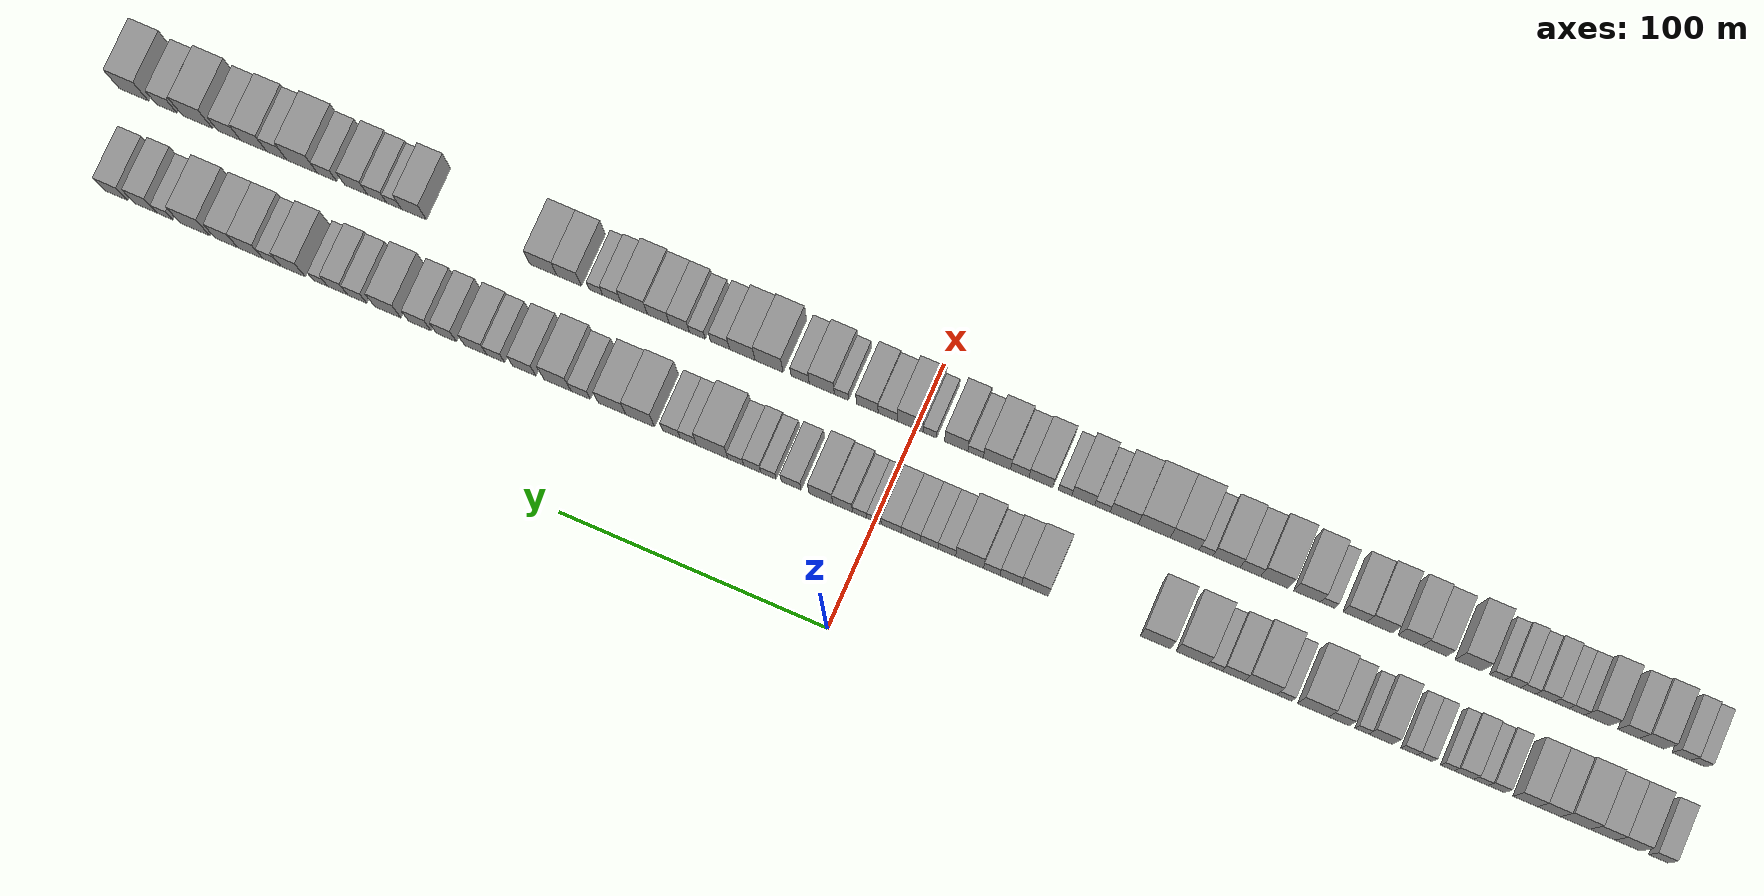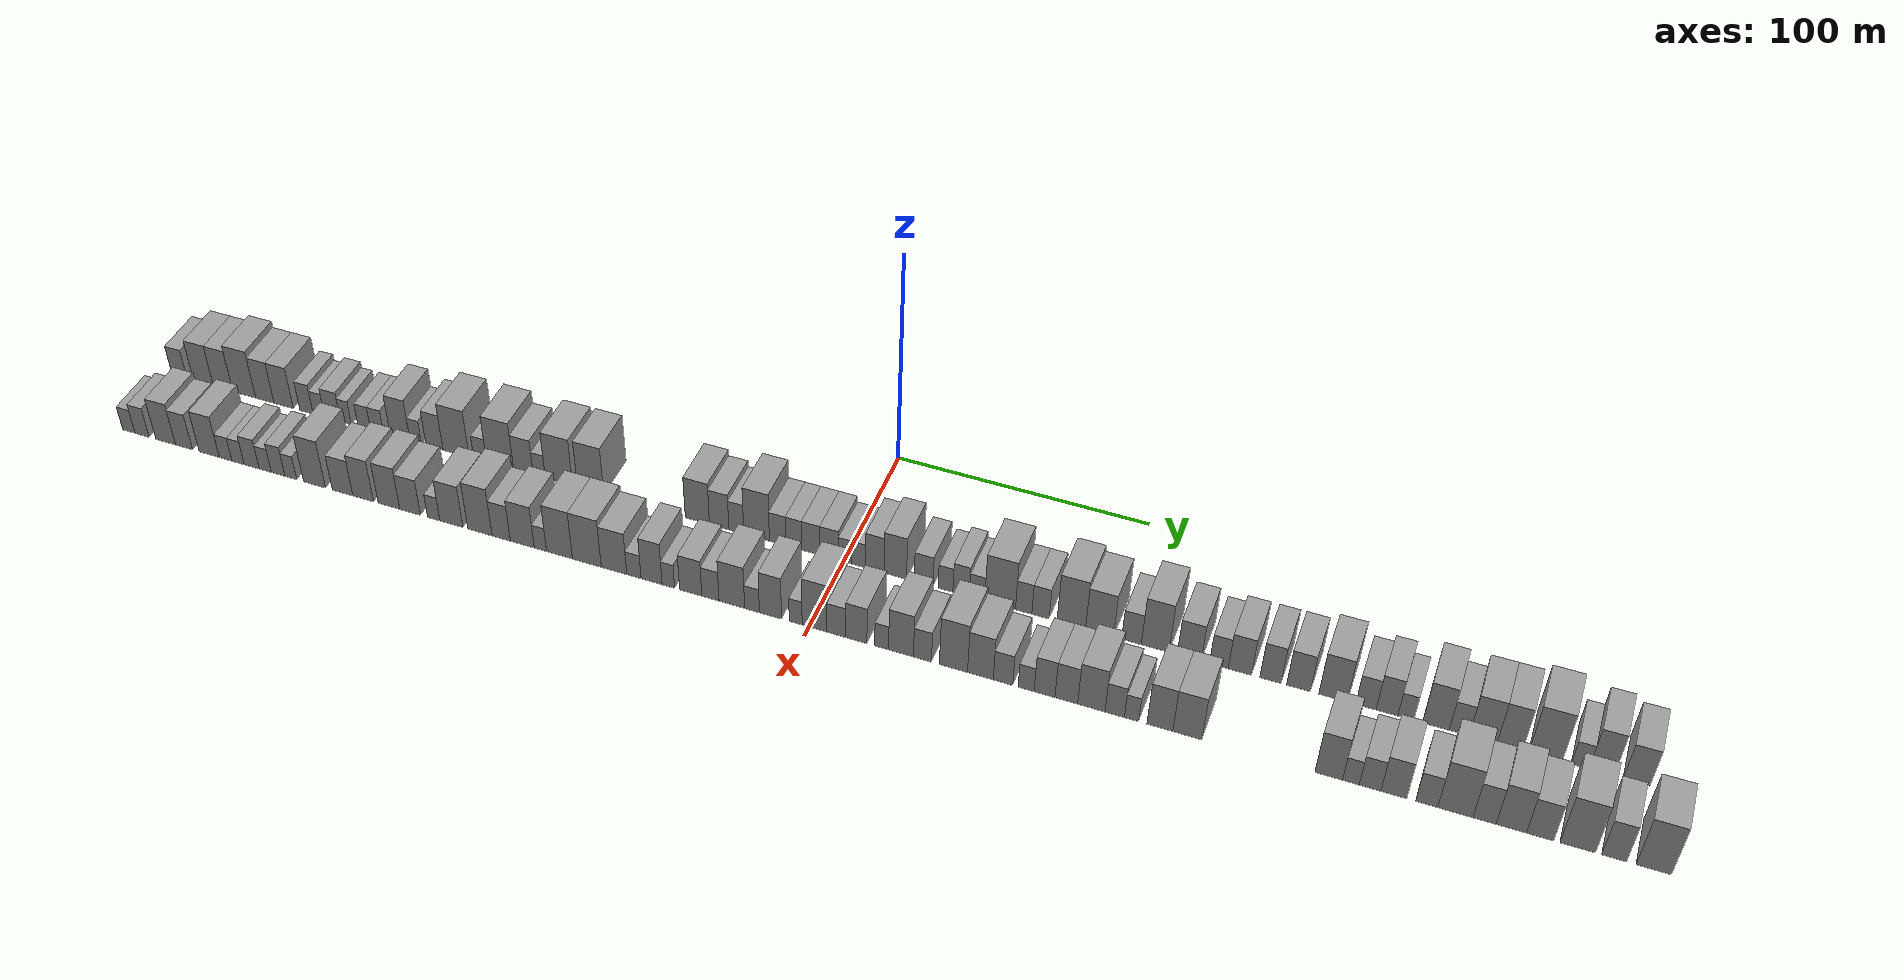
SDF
<sdf version="1.6">
 <world name="default">
  <scene>
   <sky><clouds><speed>12</speed></clouds></sky>
   <ambient>0.4 0.4 0.4 1</ambient>
   <background>0.7 0.7 0.7 1</background>
   <shadows>1</shadows>
  </scene>
  <gravity>0 0 -9.8066</gravity>
  <magnetic_field>6e-06 2.3e-05 -4.2e-05</magnetic_field>
  <physics default="0" name="default_physics" type="ode">
   <ode>
    <solver>
     <type>quick</type>
     <iters>10</iters>
     <sor>1.0</sor>
     <use_dynamic_moi_rescaling>0</use_dynamic_moi_rescaling>
    </solver>
    <constraints>
     <cfm>0</cfm>
     <erp>0.2</erp>
     <contact_max_correcting_vel>100</contact_max_correcting_vel>
     <contact_surface_layer>0.001</contact_surface_layer>
    </constraints>
   </ode>
   <max_step_size>0.004</max_step_size>
   <real_time_factor>1</real_time_factor>
   <real_time_update_rate>250</real_time_update_rate>
  </physics>
  <light name="sun" type="directional">
   <pose>0 0 10 0 0 0</pose>
   <diffuse>0.8 0.8 0.8 1</diffuse>
   <specular>0.2 0.2 0.2 1</specular>
   <attenuation>
    <range>1000</range>
    <constant>0.9</constant>
    <linear>0.01</linear>
    <quadratic>0.001</quadratic>
   </attenuation>
   <direction>-0.5 0.1 -0.9</direction>
  </light>
  <model name="building_1">
   <static>1</static>
   <pose>50.0000 -286.4982 0 0.000000 0.000000 0.000000</pose>
   <link name="link">
    <pose>0 0 7.50 0 0 0</pose>
    <collision name="collision"><geometry><box><size>20.0000 7.0036 15.0000</size></box></geometry></collision>
    <visual name="visual">
     <cast_shadows>0</cast_shadows>
     <geometry><box><size>20.0000 7.0036 15.0000</size></box></geometry>
     <material>
      <script>
       <uri>model://grey_wall/materials/scripts</uri>
       <uri>model://grey_wall/materials/textures</uri>
       <name>vrc/grey_wall</name>
      </script>
     </material>
    </visual>
   </link>
  </model>
  <model name="building_2">
   <static>1</static>
   <pose>50.0000 -275.3870 0 0.000000 0.000000 0.000000</pose>
   <link name="link">
    <pose>0 0 10.50 0 0 0</pose>
    <collision name="collision"><geometry><box><size>20.0000 9.2189 21.0000</size></box></geometry></collision>
    <visual name="visual">
     <cast_shadows>0</cast_shadows>
     <geometry><box><size>20.0000 9.2189 21.0000</size></box></geometry>
     <material>
      <script>
       <uri>model://grey_wall/materials/scripts</uri>
       <uri>model://grey_wall/materials/textures</uri>
       <name>vrc/grey_wall</name>
      </script>
     </material>
    </visual>
   </link>
  </model>
  <model name="building_3">
   <static>1</static>
   <pose>50.0000 -266.2587 0 0.000000 0.000000 0.000000</pose>
   <link name="link">
    <pose>0 0 10.50 0 0 0</pose>
    <collision name="collision"><geometry><box><size>20.0000 9.0376 21.0000</size></box></geometry></collision>
    <visual name="visual">
     <cast_shadows>0</cast_shadows>
     <geometry><box><size>20.0000 9.0376 21.0000</size></box></geometry>
     <material>
      <script>
       <uri>model://grey_wall/materials/scripts</uri>
       <uri>model://grey_wall/materials/textures</uri>
       <name>vrc/grey_wall</name>
      </script>
     </material>
    </visual>
   </link>
  </model>
  <model name="building_4">
   <static>1</static>
   <pose>50.0000 -256.4844 0 0.000000 0.000000 0.000000</pose>
   <link name="link">
    <pose>0 0 12.00 0 0 0</pose>
    <collision name="collision"><geometry><box><size>20.0000 10.5111 24.0000</size></box></geometry></collision>
    <visual name="visual">
     <cast_shadows>0</cast_shadows>
     <geometry><box><size>20.0000 10.5111 24.0000</size></box></geometry>
     <material>
      <script>
       <uri>model://grey_wall/materials/scripts</uri>
       <uri>model://grey_wall/materials/textures</uri>
       <name>vrc/grey_wall</name>
      </script>
     </material>
    </visual>
   </link>
  </model>
  <model name="building_5">
   <static>1</static>
   <pose>50.0000 -247.0157 0 0.000000 0.000000 0.000000</pose>
   <link name="link">
    <pose>0 0 10.50 0 0 0</pose>
    <collision name="collision"><geometry><box><size>20.0000 8.4264 21.0000</size></box></geometry></collision>
    <visual name="visual">
     <cast_shadows>0</cast_shadows>
     <geometry><box><size>20.0000 8.4264 21.0000</size></box></geometry>
     <material>
      <script>
       <uri>model://grey_wall/materials/scripts</uri>
       <uri>model://grey_wall/materials/textures</uri>
       <name>vrc/grey_wall</name>
      </script>
     </material>
    </visual>
   </link>
  </model>
  <model name="building_6">
   <static>1</static>
   <pose>50.0000 -238.3939 0 0.000000 0.000000 0.000000</pose>
   <link name="link">
    <pose>0 0 10.50 0 0 0</pose>
    <collision name="collision"><geometry><box><size>20.0000 8.8172 21.0000</size></box></geometry></collision>
    <visual name="visual">
     <cast_shadows>0</cast_shadows>
     <geometry><box><size>20.0000 8.8172 21.0000</size></box></geometry>
     <material>
      <script>
       <uri>model://grey_wall/materials/scripts</uri>
       <uri>model://grey_wall/materials/textures</uri>
       <name>vrc/grey_wall</name>
      </script>
     </material>
    </visual>
   </link>
  </model>
  <model name="building_7">
   <static>1</static>
   <pose>50.0000 -227.9844 0 0.000000 0.000000 0.000000</pose>
   <link name="link">
    <pose>0 0 7.50 0 0 0</pose>
    <collision name="collision"><geometry><box><size>20.0000 6.0017 15.0000</size></box></geometry></collision>
    <visual name="visual">
     <cast_shadows>0</cast_shadows>
     <geometry><box><size>20.0000 6.0017 15.0000</size></box></geometry>
     <material>
      <script>
       <uri>model://grey_wall/materials/scripts</uri>
       <uri>model://grey_wall/materials/textures</uri>
       <name>vrc/grey_wall</name>
      </script>
     </material>
    </visual>
   </link>
  </model>
  <model name="building_8">
   <static>1</static>
   <pose>50.0000 -222.3584 0 0.000000 0.000000 0.000000</pose>
   <link name="link">
    <pose>0 0 6.00 0 0 0</pose>
    <collision name="collision"><geometry><box><size>20.0000 5.2502 12.0000</size></box></geometry></collision>
    <visual name="visual">
     <cast_shadows>0</cast_shadows>
     <geometry><box><size>20.0000 5.2502 12.0000</size></box></geometry>
     <material>
      <script>
       <uri>model://grey_wall/materials/scripts</uri>
       <uri>model://grey_wall/materials/textures</uri>
       <name>vrc/grey_wall</name>
      </script>
     </material>
    </visual>
   </link>
  </model>
  <model name="building_9">
   <static>1</static>
   <pose>50.0000 -216.1610 0 0.000000 0.000000 0.000000</pose>
   <link name="link">
    <pose>0 0 7.50 0 0 0</pose>
    <collision name="collision"><geometry><box><size>20.0000 7.1447 15.0000</size></box></geometry></collision>
    <visual name="visual">
     <cast_shadows>0</cast_shadows>
     <geometry><box><size>20.0000 7.1447 15.0000</size></box></geometry>
     <material>
      <script>
       <uri>model://grey_wall/materials/scripts</uri>
       <uri>model://grey_wall/materials/textures</uri>
       <name>vrc/grey_wall</name>
      </script>
     </material>
    </visual>
   </link>
  </model>
  <model name="building_10">
   <static>1</static>
   <pose>50.0000 -210.1644 0 0.000000 0.000000 0.000000</pose>
   <link name="link">
    <pose>0 0 6.00 0 0 0</pose>
    <collision name="collision"><geometry><box><size>20.0000 4.8484 12.0000</size></box></geometry></collision>
    <visual name="visual">
     <cast_shadows>0</cast_shadows>
     <geometry><box><size>20.0000 4.8484 12.0000</size></box></geometry>
     <material>
      <script>
       <uri>model://grey_wall/materials/scripts</uri>
       <uri>model://grey_wall/materials/textures</uri>
       <name>vrc/grey_wall</name>
      </script>
     </material>
    </visual>
   </link>
  </model>
  <model name="building_11">
   <static>1</static>
   <pose>50.0000 -201.9543 0 0.000000 0.000000 0.000000</pose>
   <link name="link">
    <pose>0 0 6.00 0 0 0</pose>
    <collision name="collision"><geometry><box><size>20.0000 5.5719 12.0000</size></box></geometry></collision>
    <visual name="visual">
     <cast_shadows>0</cast_shadows>
     <geometry><box><size>20.0000 5.5719 12.0000</size></box></geometry>
     <material>
      <script>
       <uri>model://grey_wall/materials/scripts</uri>
       <uri>model://grey_wall/materials/textures</uri>
       <name>vrc/grey_wall</name>
      </script>
     </material>
    </visual>
   </link>
  </model>
  <model name="building_12">
   <static>1</static>
   <pose>50.0000 -196.2528 0 0.000000 0.000000 0.000000</pose>
   <link name="link">
    <pose>0 0 6.00 0 0 0</pose>
    <collision name="collision"><geometry><box><size>20.0000 5.8311 12.0000</size></box></geometry></collision>
    <visual name="visual">
     <cast_shadows>0</cast_shadows>
     <geometry><box><size>20.0000 5.8311 12.0000</size></box></geometry>
     <material>
      <script>
       <uri>model://grey_wall/materials/scripts</uri>
       <uri>model://grey_wall/materials/textures</uri>
       <name>vrc/grey_wall</name>
      </script>
     </material>
    </visual>
   </link>
  </model>
  <model name="building_13">
   <static>1</static>
   <pose>50.0000 -185.9787 0 0.000000 0.000000 0.000000</pose>
   <link name="link">
    <pose>0 0 10.50 0 0 0</pose>
    <collision name="collision"><geometry><box><size>20.0000 8.7171 21.0000</size></box></geometry></collision>
    <visual name="visual">
     <cast_shadows>0</cast_shadows>
     <geometry><box><size>20.0000 8.7171 21.0000</size></box></geometry>
     <material>
      <script>
       <uri>model://grey_wall/materials/scripts</uri>
       <uri>model://grey_wall/materials/textures</uri>
       <name>vrc/grey_wall</name>
      </script>
     </material>
    </visual>
   </link>
  </model>
  <model name="building_14">
   <static>1</static>
   <pose>50.0000 -179.1101 0 0.000000 0.000000 0.000000</pose>
   <link name="link">
    <pose>0 0 6.00 0 0 0</pose>
    <collision name="collision"><geometry><box><size>20.0000 5.0201 12.0000</size></box></geometry></collision>
    <visual name="visual">
     <cast_shadows>0</cast_shadows>
     <geometry><box><size>20.0000 5.0201 12.0000</size></box></geometry>
     <material>
      <script>
       <uri>model://grey_wall/materials/scripts</uri>
       <uri>model://grey_wall/materials/textures</uri>
       <name>vrc/grey_wall</name>
      </script>
     </material>
    </visual>
   </link>
  </model>
  <model name="building_15">
   <static>1</static>
   <pose>50.0000 -170.8484 0 0.000000 0.000000 0.000000</pose>
   <link name="link">
    <pose>0 0 9.00 0 0 0</pose>
    <collision name="collision"><geometry><box><size>20.0000 7.5033 18.0000</size></box></geometry></collision>
    <visual name="visual">
     <cast_shadows>0</cast_shadows>
     <geometry><box><size>20.0000 7.5033 18.0000</size></box></geometry>
     <material>
      <script>
       <uri>model://grey_wall/materials/scripts</uri>
       <uri>model://grey_wall/materials/textures</uri>
       <name>vrc/grey_wall</name>
      </script>
     </material>
    </visual>
   </link>
  </model>
  <model name="building_16">
   <static>1</static>
   <pose>50.0000 -161.3963 0 0.000000 0.000000 0.000000</pose>
   <link name="link">
    <pose>0 0 12.00 0 0 0</pose>
    <collision name="collision"><geometry><box><size>20.0000 11.4009 24.0000</size></box></geometry></collision>
    <visual name="visual">
     <cast_shadows>0</cast_shadows>
     <geometry><box><size>20.0000 11.4009 24.0000</size></box></geometry>
     <material>
      <script>
       <uri>model://grey_wall/materials/scripts</uri>
       <uri>model://grey_wall/materials/textures</uri>
       <name>vrc/grey_wall</name>
      </script>
     </material>
    </visual>
   </link>
  </model>
  <model name="building_17">
   <static>1</static>
   <pose>50.0000 -150.9021 0 0.000000 0.000000 0.000000</pose>
   <link name="link">
    <pose>0 0 6.00 0 0 0</pose>
    <collision name="collision"><geometry><box><size>20.0000 5.5875 12.0000</size></box></geometry></collision>
    <visual name="visual">
     <cast_shadows>0</cast_shadows>
     <geometry><box><size>20.0000 5.5875 12.0000</size></box></geometry>
     <material>
      <script>
       <uri>model://grey_wall/materials/scripts</uri>
       <uri>model://grey_wall/materials/textures</uri>
       <name>vrc/grey_wall</name>
      </script>
     </material>
    </visual>
   </link>
  </model>
  <model name="building_18">
   <static>1</static>
   <pose>50.0000 -142.2736 0 0.000000 0.000000 0.000000</pose>
   <link name="link">
    <pose>0 0 12.00 0 0 0</pose>
    <collision name="collision"><geometry><box><size>20.0000 11.6695 24.0000</size></box></geometry></collision>
    <visual name="visual">
     <cast_shadows>0</cast_shadows>
     <geometry><box><size>20.0000 11.6695 24.0000</size></box></geometry>
     <material>
      <script>
       <uri>model://grey_wall/materials/scripts</uri>
       <uri>model://grey_wall/materials/textures</uri>
       <name>vrc/grey_wall</name>
      </script>
     </material>
    </visual>
   </link>
  </model>
  <model name="building_19">
   <static>1</static>
   <pose>50.0000 -132.2392 0 0.000000 0.000000 0.000000</pose>
   <link name="link">
    <pose>0 0 9.00 0 0 0</pose>
    <collision name="collision"><geometry><box><size>20.0000 8.3993 18.0000</size></box></geometry></collision>
    <visual name="visual">
     <cast_shadows>0</cast_shadows>
     <geometry><box><size>20.0000 8.3993 18.0000</size></box></geometry>
     <material>
      <script>
       <uri>model://grey_wall/materials/scripts</uri>
       <uri>model://grey_wall/materials/textures</uri>
       <name>vrc/grey_wall</name>
      </script>
     </material>
    </visual>
   </link>
  </model>
  <model name="building_20">
   <static>1</static>
   <pose>50.0000 -125.4247 0 0.000000 0.000000 0.000000</pose>
   <link name="link">
    <pose>0 0 6.00 0 0 0</pose>
    <collision name="collision"><geometry><box><size>20.0000 5.2296 12.0000</size></box></geometry></collision>
    <visual name="visual">
     <cast_shadows>0</cast_shadows>
     <geometry><box><size>20.0000 5.2296 12.0000</size></box></geometry>
     <material>
      <script>
       <uri>model://grey_wall/materials/scripts</uri>
       <uri>model://grey_wall/materials/textures</uri>
       <name>vrc/grey_wall</name>
      </script>
     </material>
    </visual>
   </link>
  </model>
  <model name="building_21">
   <static>1</static>
   <pose>50.0000 -117.0029 0 0.000000 0.000000 0.000000</pose>
   <link name="link">
    <pose>0 0 12.00 0 0 0</pose>
    <collision name="collision"><geometry><box><size>20.0000 11.6140 24.0000</size></box></geometry></collision>
    <visual name="visual">
     <cast_shadows>0</cast_shadows>
     <geometry><box><size>20.0000 11.6140 24.0000</size></box></geometry>
     <material>
      <script>
       <uri>model://grey_wall/materials/scripts</uri>
       <uri>model://grey_wall/materials/textures</uri>
       <name>vrc/grey_wall</name>
      </script>
     </material>
    </visual>
   </link>
  </model>
  <model name="building_22">
   <static>1</static>
   <pose>50.0000 -103.6227 0 0.000000 0.000000 0.000000</pose>
   <link name="link">
    <pose>0 0 12.00 0 0 0</pose>
    <collision name="collision"><geometry><box><size>20.0000 11.1463 24.0000</size></box></geometry></collision>
    <visual name="visual">
     <cast_shadows>0</cast_shadows>
     <geometry><box><size>20.0000 11.1463 24.0000</size></box></geometry>
     <material>
      <script>
       <uri>model://grey_wall/materials/scripts</uri>
       <uri>model://grey_wall/materials/textures</uri>
       <name>vrc/grey_wall</name>
      </script>
     </material>
    </visual>
   </link>
  </model>
  <model name="building_23">
   <static>1</static>
   <pose>50.0000 -59.1376 0 0.000000 0.000000 0.000000</pose>
   <link name="link">
    <pose>0 0 10.50 0 0 0</pose>
    <collision name="collision"><geometry><box><size>20.0000 9.9413 21.0000</size></box></geometry></collision>
    <visual name="visual">
     <cast_shadows>0</cast_shadows>
     <geometry><box><size>20.0000 9.9413 21.0000</size></box></geometry>
     <material>
      <script>
       <uri>model://grey_wall/materials/scripts</uri>
       <uri>model://grey_wall/materials/textures</uri>
       <name>vrc/grey_wall</name>
      </script>
     </material>
    </visual>
   </link>
  </model>
  <model name="building_24">
   <static>1</static>
   <pose>50.0000 -50.2014 0 0.000000 0.000000 0.000000</pose>
   <link name="link">
    <pose>0 0 9.00 0 0 0</pose>
    <collision name="collision"><geometry><box><size>20.0000 7.9310 18.0000</size></box></geometry></collision>
    <visual name="visual">
     <cast_shadows>0</cast_shadows>
     <geometry><box><size>20.0000 7.9310 18.0000</size></box></geometry>
     <material>
      <script>
       <uri>model://grey_wall/materials/scripts</uri>
       <uri>model://grey_wall/materials/textures</uri>
       <name>vrc/grey_wall</name>
      </script>
     </material>
    </visual>
   </link>
  </model>
  <model name="building_25">
   <static>1</static>
   <pose>50.0000 -43.1942 0 0.000000 0.000000 0.000000</pose>
   <link name="link">
    <pose>0 0 7.50 0 0 0</pose>
    <collision name="collision"><geometry><box><size>20.0000 6.0834 15.0000</size></box></geometry></collision>
    <visual name="visual">
     <cast_shadows>0</cast_shadows>
     <geometry><box><size>20.0000 6.0834 15.0000</size></box></geometry>
     <material>
      <script>
       <uri>model://grey_wall/materials/scripts</uri>
       <uri>model://grey_wall/materials/textures</uri>
       <name>vrc/grey_wall</name>
      </script>
     </material>
    </visual>
   </link>
  </model>
  <model name="building_26">
   <static>1</static>
   <pose>50.0000 -34.9737 0 0.000000 0.000000 0.000000</pose>
   <link name="link">
    <pose>0 0 12.00 0 0 0</pose>
    <collision name="collision"><geometry><box><size>20.0000 10.3576 24.0000</size></box></geometry></collision>
    <visual name="visual">
     <cast_shadows>0</cast_shadows>
     <geometry><box><size>20.0000 10.3576 24.0000</size></box></geometry>
     <material>
      <script>
       <uri>model://grey_wall/materials/scripts</uri>
       <uri>model://grey_wall/materials/textures</uri>
       <name>vrc/grey_wall</name>
      </script>
     </material>
    </visual>
   </link>
  </model>
  <model name="building_27">
   <static>1</static>
   <pose>50.0000 -26.5059 0 0.000000 0.000000 0.000000</pose>
   <link name="link">
    <pose>0 0 7.50 0 0 0</pose>
    <collision name="collision"><geometry><box><size>20.0000 6.5779 15.0000</size></box></geometry></collision>
    <visual name="visual">
     <cast_shadows>0</cast_shadows>
     <geometry><box><size>20.0000 6.5779 15.0000</size></box></geometry>
     <material>
      <script>
       <uri>model://grey_wall/materials/scripts</uri>
       <uri>model://grey_wall/materials/textures</uri>
       <name>vrc/grey_wall</name>
      </script>
     </material>
    </visual>
   </link>
  </model>
  <model name="building_28">
   <static>1</static>
   <pose>50.0000 -19.9818 0 0.000000 0.000000 0.000000</pose>
   <link name="link">
    <pose>0 0 7.50 0 0 0</pose>
    <collision name="collision"><geometry><box><size>20.0000 6.4703 15.0000</size></box></geometry></collision>
    <visual name="visual">
     <cast_shadows>0</cast_shadows>
     <geometry><box><size>20.0000 6.4703 15.0000</size></box></geometry>
     <material>
      <script>
       <uri>model://grey_wall/materials/scripts</uri>
       <uri>model://grey_wall/materials/textures</uri>
       <name>vrc/grey_wall</name>
      </script>
     </material>
    </visual>
   </link>
  </model>
  <model name="building_29">
   <static>1</static>
   <pose>50.0000 -13.1419 0 0.000000 0.000000 0.000000</pose>
   <link name="link">
    <pose>0 0 7.50 0 0 0</pose>
    <collision name="collision"><geometry><box><size>20.0000 7.2096 15.0000</size></box></geometry></collision>
    <visual name="visual">
     <cast_shadows>0</cast_shadows>
     <geometry><box><size>20.0000 7.2096 15.0000</size></box></geometry>
     <material>
      <script>
       <uri>model://grey_wall/materials/scripts</uri>
       <uri>model://grey_wall/materials/textures</uri>
       <name>vrc/grey_wall</name>
      </script>
     </material>
    </visual>
   </link>
  </model>
  <model name="building_30">
   <static>1</static>
   <pose>50.0000 -5.8163 0 0.000000 0.000000 0.000000</pose>
   <link name="link">
    <pose>0 0 7.50 0 0 0</pose>
    <collision name="collision"><geometry><box><size>20.0000 7.4415 15.0000</size></box></geometry></collision>
    <visual name="visual">
     <cast_shadows>0</cast_shadows>
     <geometry><box><size>20.0000 7.4415 15.0000</size></box></geometry>
     <material>
      <script>
       <uri>model://grey_wall/materials/scripts</uri>
       <uri>model://grey_wall/materials/textures</uri>
       <name>vrc/grey_wall</name>
      </script>
     </material>
    </visual>
   </link>
  </model>
  <model name="building_31">
   <static>1</static>
   <pose>50.0000 0.5402 0 0.000000 0.000000 0.000000</pose>
   <link name="link">
    <pose>0 0 6.00 0 0 0</pose>
    <collision name="collision"><geometry><box><size>20.0000 5.2715 12.0000</size></box></geometry></collision>
    <visual name="visual">
     <cast_shadows>0</cast_shadows>
     <geometry><box><size>20.0000 5.2715 12.0000</size></box></geometry>
     <material>
      <script>
       <uri>model://grey_wall/materials/scripts</uri>
       <uri>model://grey_wall/materials/textures</uri>
       <name>vrc/grey_wall</name>
      </script>
     </material>
    </visual>
   </link>
  </model>
  <model name="building_32">
   <static>1</static>
   <pose>50.0000 5.8789 0 0.000000 0.000000 0.000000</pose>
   <link name="link">
    <pose>0 0 6.00 0 0 0</pose>
    <collision name="collision"><geometry><box><size>20.0000 5.4058 12.0000</size></box></geometry></collision>
    <visual name="visual">
     <cast_shadows>0</cast_shadows>
     <geometry><box><size>20.0000 5.4058 12.0000</size></box></geometry>
     <material>
      <script>
       <uri>model://grey_wall/materials/scripts</uri>
       <uri>model://grey_wall/materials/textures</uri>
       <name>vrc/grey_wall</name>
      </script>
     </material>
    </visual>
   </link>
  </model>
  <model name="building_33">
   <static>1</static>
   <pose>50.0000 12.2712 0 0.000000 0.000000 0.000000</pose>
   <link name="link">
    <pose>0 0 9.00 0 0 0</pose>
    <collision name="collision"><geometry><box><size>20.0000 7.3789 18.0000</size></box></geometry></collision>
    <visual name="visual">
     <cast_shadows>0</cast_shadows>
     <geometry><box><size>20.0000 7.3789 18.0000</size></box></geometry>
     <material>
      <script>
       <uri>model://grey_wall/materials/scripts</uri>
       <uri>model://grey_wall/materials/textures</uri>
       <name>vrc/grey_wall</name>
      </script>
     </material>
    </visual>
   </link>
  </model>
  <model name="building_34">
   <static>1</static>
   <pose>50.0000 20.3390 0 0.000000 0.000000 0.000000</pose>
   <link name="link">
    <pose>0 0 10.50 0 0 0</pose>
    <collision name="collision"><geometry><box><size>20.0000 8.7569 21.0000</size></box></geometry></collision>
    <visual name="visual">
     <cast_shadows>0</cast_shadows>
     <geometry><box><size>20.0000 8.7569 21.0000</size></box></geometry>
     <material>
      <script>
       <uri>model://grey_wall/materials/scripts</uri>
       <uri>model://grey_wall/materials/textures</uri>
       <name>vrc/grey_wall</name>
      </script>
     </material>
    </visual>
   </link>
  </model>
  <model name="building_35">
   <static>1</static>
   <pose>50.0000 31.3894 0 0.000000 0.000000 0.000000</pose>
   <link name="link">
    <pose>0 0 7.50 0 0 0</pose>
    <collision name="collision"><geometry><box><size>20.0000 7.3439 15.0000</size></box></geometry></collision>
    <visual name="visual">
     <cast_shadows>0</cast_shadows>
     <geometry><box><size>20.0000 7.3439 15.0000</size></box></geometry>
     <material>
      <script>
       <uri>model://grey_wall/materials/scripts</uri>
       <uri>model://grey_wall/materials/textures</uri>
       <name>vrc/grey_wall</name>
      </script>
     </material>
    </visual>
   </link>
  </model>
  <model name="building_36">
   <static>1</static>
   <pose>50.0000 39.9124 0 0.000000 0.000000 0.000000</pose>
   <link name="link">
    <pose>0 0 6.00 0 0 0</pose>
    <collision name="collision"><geometry><box><size>20.0000 5.7020 12.0000</size></box></geometry></collision>
    <visual name="visual">
     <cast_shadows>0</cast_shadows>
     <geometry><box><size>20.0000 5.7020 12.0000</size></box></geometry>
     <material>
      <script>
       <uri>model://grey_wall/materials/scripts</uri>
       <uri>model://grey_wall/materials/textures</uri>
       <name>vrc/grey_wall</name>
      </script>
     </material>
    </visual>
   </link>
  </model>
  <model name="building_37">
   <static>1</static>
   <pose>50.0000 45.9449 0 0.000000 0.000000 0.000000</pose>
   <link name="link">
    <pose>0 0 7.50 0 0 0</pose>
    <collision name="collision"><geometry><box><size>20.0000 6.3630 15.0000</size></box></geometry></collision>
    <visual name="visual">
     <cast_shadows>0</cast_shadows>
     <geometry><box><size>20.0000 6.3630 15.0000</size></box></geometry>
     <material>
      <script>
       <uri>model://grey_wall/materials/scripts</uri>
       <uri>model://grey_wall/materials/textures</uri>
       <name>vrc/grey_wall</name>
      </script>
     </material>
    </visual>
   </link>
  </model>
  <model name="building_38">
   <static>1</static>
   <pose>50.0000 52.0841 0 0.000000 0.000000 0.000000</pose>
   <link name="link">
    <pose>0 0 6.00 0 0 0</pose>
    <collision name="collision"><geometry><box><size>20.0000 5.9154 12.0000</size></box></geometry></collision>
    <visual name="visual">
     <cast_shadows>0</cast_shadows>
     <geometry><box><size>20.0000 5.9154 12.0000</size></box></geometry>
     <material>
      <script>
       <uri>model://grey_wall/materials/scripts</uri>
       <uri>model://grey_wall/materials/textures</uri>
       <name>vrc/grey_wall</name>
      </script>
     </material>
    </visual>
   </link>
  </model>
  <model name="building_39">
   <static>1</static>
   <pose>50.0000 60.9253 0 0.000000 0.000000 0.000000</pose>
   <link name="link">
    <pose>0 0 12.00 0 0 0</pose>
    <collision name="collision"><geometry><box><size>20.0000 11.7671 24.0000</size></box></geometry></collision>
    <visual name="visual">
     <cast_shadows>0</cast_shadows>
     <geometry><box><size>20.0000 11.7671 24.0000</size></box></geometry>
     <material>
      <script>
       <uri>model://grey_wall/materials/scripts</uri>
       <uri>model://grey_wall/materials/textures</uri>
       <name>vrc/grey_wall</name>
      </script>
     </material>
    </visual>
   </link>
  </model>
  <model name="building_40">
   <static>1</static>
   <pose>50.0000 69.9162 0 0.000000 0.000000 0.000000</pose>
   <link name="link">
    <pose>0 0 7.50 0 0 0</pose>
    <collision name="collision"><geometry><box><size>20.0000 6.2145 15.0000</size></box></geometry></collision>
    <visual name="visual">
     <cast_shadows>0</cast_shadows>
     <geometry><box><size>20.0000 6.2145 15.0000</size></box></geometry>
     <material>
      <script>
       <uri>model://grey_wall/materials/scripts</uri>
       <uri>model://grey_wall/materials/textures</uri>
       <name>vrc/grey_wall</name>
      </script>
     </material>
    </visual>
   </link>
  </model>
  <model name="building_41">
   <static>1</static>
   <pose>50.0000 76.3128 0 0.000000 0.000000 0.000000</pose>
   <link name="link">
    <pose>0 0 7.50 0 0 0</pose>
    <collision name="collision"><geometry><box><size>20.0000 6.5787 15.0000</size></box></geometry></collision>
    <visual name="visual">
     <cast_shadows>0</cast_shadows>
     <geometry><box><size>20.0000 6.5787 15.0000</size></box></geometry>
     <material>
      <script>
       <uri>model://grey_wall/materials/scripts</uri>
       <uri>model://grey_wall/materials/textures</uri>
       <name>vrc/grey_wall</name>
      </script>
     </material>
    </visual>
   </link>
  </model>
  <model name="building_42">
   <static>1</static>
   <pose>50.0000 87.9561 0 0.000000 0.000000 0.000000</pose>
   <link name="link">
    <pose>0 0 12.00 0 0 0</pose>
    <collision name="collision"><geometry><box><size>20.0000 10.7080 24.0000</size></box></geometry></collision>
    <visual name="visual">
     <cast_shadows>0</cast_shadows>
     <geometry><box><size>20.0000 10.7080 24.0000</size></box></geometry>
     <material>
      <script>
       <uri>model://grey_wall/materials/scripts</uri>
       <uri>model://grey_wall/materials/textures</uri>
       <name>vrc/grey_wall</name>
      </script>
     </material>
    </visual>
   </link>
  </model>
  <model name="building_43">
   <static>1</static>
   <pose>50.0000 98.5569 0 0.000000 0.000000 0.000000</pose>
   <link name="link">
    <pose>0 0 10.50 0 0 0</pose>
    <collision name="collision"><geometry><box><size>20.0000 10.4936 21.0000</size></box></geometry></collision>
    <visual name="visual">
     <cast_shadows>0</cast_shadows>
     <geometry><box><size>20.0000 10.4936 21.0000</size></box></geometry>
     <material>
      <script>
       <uri>model://grey_wall/materials/scripts</uri>
       <uri>model://grey_wall/materials/textures</uri>
       <name>vrc/grey_wall</name>
      </script>
     </material>
    </visual>
   </link>
  </model>
  <model name="building_44">
   <static>1</static>
   <pose>50.0000 110.4333 0 0.000000 0.000000 0.000000</pose>
   <link name="link">
    <pose>0 0 7.50 0 0 0</pose>
    <collision name="collision"><geometry><box><size>20.0000 7.2592 15.0000</size></box></geometry></collision>
    <visual name="visual">
     <cast_shadows>0</cast_shadows>
     <geometry><box><size>20.0000 7.2592 15.0000</size></box></geometry>
     <material>
      <script>
       <uri>model://grey_wall/materials/scripts</uri>
       <uri>model://grey_wall/materials/textures</uri>
       <name>vrc/grey_wall</name>
      </script>
     </material>
    </visual>
   </link>
  </model>
  <model name="building_45">
   <static>1</static>
   <pose>50.0000 119.1959 0 0.000000 0.000000 0.000000</pose>
   <link name="link">
    <pose>0 0 12.00 0 0 0</pose>
    <collision name="collision"><geometry><box><size>20.0000 10.2659 24.0000</size></box></geometry></collision>
    <visual name="visual">
     <cast_shadows>0</cast_shadows>
     <geometry><box><size>20.0000 10.2659 24.0000</size></box></geometry>
     <material>
      <script>
       <uri>model://grey_wall/materials/scripts</uri>
       <uri>model://grey_wall/materials/textures</uri>
       <name>vrc/grey_wall</name>
      </script>
     </material>
    </visual>
   </link>
  </model>
  <model name="building_46">
   <static>1</static>
   <pose>50.0000 131.7334 0 0.000000 0.000000 0.000000</pose>
   <link name="link">
    <pose>0 0 9.00 0 0 0</pose>
    <collision name="collision"><geometry><box><size>20.0000 8.8091 18.0000</size></box></geometry></collision>
    <visual name="visual">
     <cast_shadows>0</cast_shadows>
     <geometry><box><size>20.0000 8.8091 18.0000</size></box></geometry>
     <material>
      <script>
       <uri>model://grey_wall/materials/scripts</uri>
       <uri>model://grey_wall/materials/textures</uri>
       <name>vrc/grey_wall</name>
      </script>
     </material>
    </visual>
   </link>
  </model>
  <model name="building_47">
   <static>1</static>
   <pose>50.0000 142.5365 0 0.000000 0.000000 0.000000</pose>
   <link name="link">
    <pose>0 0 7.50 0 0 0</pose>
    <collision name="collision"><geometry><box><size>20.0000 6.7971 15.0000</size></box></geometry></collision>
    <visual name="visual">
     <cast_shadows>0</cast_shadows>
     <geometry><box><size>20.0000 6.7971 15.0000</size></box></geometry>
     <material>
      <script>
       <uri>model://grey_wall/materials/scripts</uri>
       <uri>model://grey_wall/materials/textures</uri>
       <name>vrc/grey_wall</name>
      </script>
     </material>
    </visual>
   </link>
  </model>
  <model name="building_48">
   <static>1</static>
   <pose>50.0000 150.1659 0 0.000000 0.000000 0.000000</pose>
   <link name="link">
    <pose>0 0 9.00 0 0 0</pose>
    <collision name="collision"><geometry><box><size>20.0000 8.4616 18.0000</size></box></geometry></collision>
    <visual name="visual">
     <cast_shadows>0</cast_shadows>
     <geometry><box><size>20.0000 8.4616 18.0000</size></box></geometry>
     <material>
      <script>
       <uri>model://grey_wall/materials/scripts</uri>
       <uri>model://grey_wall/materials/textures</uri>
       <name>vrc/grey_wall</name>
      </script>
     </material>
    </visual>
   </link>
  </model>
  <model name="building_49">
   <static>1</static>
   <pose>50.0000 161.2245 0 0.000000 0.000000 0.000000</pose>
   <link name="link">
    <pose>0 0 9.00 0 0 0</pose>
    <collision name="collision"><geometry><box><size>20.0000 7.6556 18.0000</size></box></geometry></collision>
    <visual name="visual">
     <cast_shadows>0</cast_shadows>
     <geometry><box><size>20.0000 7.6556 18.0000</size></box></geometry>
     <material>
      <script>
       <uri>model://grey_wall/materials/scripts</uri>
       <uri>model://grey_wall/materials/textures</uri>
       <name>vrc/grey_wall</name>
      </script>
     </material>
    </visual>
   </link>
  </model>
  <model name="building_50">
   <static>1</static>
   <pose>50.0000 171.2923 0 0.000000 0.000000 0.000000</pose>
   <link name="link">
    <pose>0 0 9.00 0 0 0</pose>
    <collision name="collision"><geometry><box><size>20.0000 8.4799 18.0000</size></box></geometry></collision>
    <visual name="visual">
     <cast_shadows>0</cast_shadows>
     <geometry><box><size>20.0000 8.4799 18.0000</size></box></geometry>
     <material>
      <script>
       <uri>model://grey_wall/materials/scripts</uri>
       <uri>model://grey_wall/materials/textures</uri>
       <name>vrc/grey_wall</name>
      </script>
     </material>
    </visual>
   </link>
  </model>
  <model name="building_51">
   <static>1</static>
   <pose>50.0000 183.5639 0 0.000000 0.000000 0.000000</pose>
   <link name="link">
    <pose>0 0 10.50 0 0 0</pose>
    <collision name="collision"><geometry><box><size>20.0000 10.0632 21.0000</size></box></geometry></collision>
    <visual name="visual">
     <cast_shadows>0</cast_shadows>
     <geometry><box><size>20.0000 10.0632 21.0000</size></box></geometry>
     <material>
      <script>
       <uri>model://grey_wall/materials/scripts</uri>
       <uri>model://grey_wall/materials/textures</uri>
       <name>vrc/grey_wall</name>
      </script>
     </material>
    </visual>
   </link>
  </model>
  <model name="building_52">
   <static>1</static>
   <pose>50.0000 195.1782 0 0.000000 0.000000 0.000000</pose>
   <link name="link">
    <pose>0 0 7.50 0 0 0</pose>
    <collision name="collision"><geometry><box><size>20.0000 7.1654 15.0000</size></box></geometry></collision>
    <visual name="visual">
     <cast_shadows>0</cast_shadows>
     <geometry><box><size>20.0000 7.1654 15.0000</size></box></geometry>
     <material>
      <script>
       <uri>model://grey_wall/materials/scripts</uri>
       <uri>model://grey_wall/materials/textures</uri>
       <name>vrc/grey_wall</name>
      </script>
     </material>
    </visual>
   </link>
  </model>
  <model name="building_53">
   <static>1</static>
   <pose>50.0000 202.5631 0 0.000000 0.000000 0.000000</pose>
   <link name="link">
    <pose>0 0 9.00 0 0 0</pose>
    <collision name="collision"><geometry><box><size>20.0000 7.6042 18.0000</size></box></geometry></collision>
    <visual name="visual">
     <cast_shadows>0</cast_shadows>
     <geometry><box><size>20.0000 7.6042 18.0000</size></box></geometry>
     <material>
      <script>
       <uri>model://grey_wall/materials/scripts</uri>
       <uri>model://grey_wall/materials/textures</uri>
       <name>vrc/grey_wall</name>
      </script>
     </material>
    </visual>
   </link>
  </model>
  <model name="building_54">
   <static>1</static>
   <pose>50.0000 209.1715 0 0.000000 0.000000 0.000000</pose>
   <link name="link">
    <pose>0 0 6.00 0 0 0</pose>
    <collision name="collision"><geometry><box><size>20.0000 5.6125 12.0000</size></box></geometry></collision>
    <visual name="visual">
     <cast_shadows>0</cast_shadows>
     <geometry><box><size>20.0000 5.6125 12.0000</size></box></geometry>
     <material>
      <script>
       <uri>model://grey_wall/materials/scripts</uri>
       <uri>model://grey_wall/materials/textures</uri>
       <name>vrc/grey_wall</name>
      </script>
     </material>
    </visual>
   </link>
  </model>
  <model name="building_55">
   <static>1</static>
   <pose>50.0000 219.5909 0 0.000000 0.000000 0.000000</pose>
   <link name="link">
    <pose>0 0 10.50 0 0 0</pose>
    <collision name="collision"><geometry><box><size>20.0000 9.2264 21.0000</size></box></geometry></collision>
    <visual name="visual">
     <cast_shadows>0</cast_shadows>
     <geometry><box><size>20.0000 9.2264 21.0000</size></box></geometry>
     <material>
      <script>
       <uri>model://grey_wall/materials/scripts</uri>
       <uri>model://grey_wall/materials/textures</uri>
       <name>vrc/grey_wall</name>
      </script>
     </material>
    </visual>
   </link>
  </model>
  <model name="building_56">
   <static>1</static>
   <pose>50.0000 227.6400 0 0.000000 0.000000 0.000000</pose>
   <link name="link">
    <pose>0 0 7.50 0 0 0</pose>
    <collision name="collision"><geometry><box><size>20.0000 6.8717 15.0000</size></box></geometry></collision>
    <visual name="visual">
     <cast_shadows>0</cast_shadows>
     <geometry><box><size>20.0000 6.8717 15.0000</size></box></geometry>
     <material>
      <script>
       <uri>model://grey_wall/materials/scripts</uri>
       <uri>model://grey_wall/materials/textures</uri>
       <name>vrc/grey_wall</name>
      </script>
     </material>
    </visual>
   </link>
  </model>
  <model name="building_57">
   <static>1</static>
   <pose>50.0000 235.8443 0 0.000000 0.000000 0.000000</pose>
   <link name="link">
    <pose>0 0 10.50 0 0 0</pose>
    <collision name="collision"><geometry><box><size>20.0000 9.5370 21.0000</size></box></geometry></collision>
    <visual name="visual">
     <cast_shadows>0</cast_shadows>
     <geometry><box><size>20.0000 9.5370 21.0000</size></box></geometry>
     <material>
      <script>
       <uri>model://grey_wall/materials/scripts</uri>
       <uri>model://grey_wall/materials/textures</uri>
       <name>vrc/grey_wall</name>
      </script>
     </material>
    </visual>
   </link>
  </model>
  <model name="building_58">
   <static>1</static>
   <pose>50.0000 244.9962 0 0.000000 0.000000 0.000000</pose>
   <link name="link">
    <pose>0 0 10.50 0 0 0</pose>
    <collision name="collision"><geometry><box><size>20.0000 8.7669 21.0000</size></box></geometry></collision>
    <visual name="visual">
     <cast_shadows>0</cast_shadows>
     <geometry><box><size>20.0000 8.7669 21.0000</size></box></geometry>
     <material>
      <script>
       <uri>model://grey_wall/materials/scripts</uri>
       <uri>model://grey_wall/materials/textures</uri>
       <name>vrc/grey_wall</name>
      </script>
     </material>
    </visual>
   </link>
  </model>
  <model name="building_59">
   <static>1</static>
   <pose>50.0000 257.0644 0 0.000000 0.000000 0.000000</pose>
   <link name="link">
    <pose>0 0 12.00 0 0 0</pose>
    <collision name="collision"><geometry><box><size>20.0000 11.3694 24.0000</size></box></geometry></collision>
    <visual name="visual">
     <cast_shadows>0</cast_shadows>
     <geometry><box><size>20.0000 11.3694 24.0000</size></box></geometry>
     <material>
      <script>
       <uri>model://grey_wall/materials/scripts</uri>
       <uri>model://grey_wall/materials/textures</uri>
       <name>vrc/grey_wall</name>
      </script>
     </material>
    </visual>
   </link>
  </model>
  <model name="building_60">
   <static>1</static>
   <pose>50.0000 268.7016 0 0.000000 0.000000 0.000000</pose>
   <link name="link">
    <pose>0 0 6.00 0 0 0</pose>
    <collision name="collision"><geometry><box><size>20.0000 5.9051 12.0000</size></box></geometry></collision>
    <visual name="visual">
     <cast_shadows>0</cast_shadows>
     <geometry><box><size>20.0000 5.9051 12.0000</size></box></geometry>
     <material>
      <script>
       <uri>model://grey_wall/materials/scripts</uri>
       <uri>model://grey_wall/materials/textures</uri>
       <name>vrc/grey_wall</name>
      </script>
     </material>
    </visual>
   </link>
  </model>
  <model name="building_61">
   <static>1</static>
   <pose>50.0000 275.8847 0 0.000000 0.000000 0.000000</pose>
   <link name="link">
    <pose>0 0 10.50 0 0 0</pose>
    <collision name="collision"><geometry><box><size>20.0000 8.4611 21.0000</size></box></geometry></collision>
    <visual name="visual">
     <cast_shadows>0</cast_shadows>
     <geometry><box><size>20.0000 8.4611 21.0000</size></box></geometry>
     <material>
      <script>
       <uri>model://grey_wall/materials/scripts</uri>
       <uri>model://grey_wall/materials/textures</uri>
       <name>vrc/grey_wall</name>
      </script>
     </material>
    </visual>
   </link>
  </model>
  <model name="building_62">
   <static>1</static>
   <pose>50.0000 287.5691 0 0.000000 0.000000 0.000000</pose>
   <link name="link">
    <pose>0 0 9.00 0 0 0</pose>
    <collision name="collision"><geometry><box><size>20.0000 8.9076 18.0000</size></box></geometry></collision>
    <visual name="visual">
     <cast_shadows>0</cast_shadows>
     <geometry><box><size>20.0000 8.9076 18.0000</size></box></geometry>
     <material>
      <script>
       <uri>model://grey_wall/materials/scripts</uri>
       <uri>model://grey_wall/materials/textures</uri>
       <name>vrc/grey_wall</name>
      </script>
     </material>
    </visual>
   </link>
  </model>
  <model name="building_63">
   <static>1</static>
   <pose>85.0000 -287.1924 0 0.000000 0.000000 0.000000</pose>
   <link name="link">
    <pose>0 0 6.00 0 0 0</pose>
    <collision name="collision"><geometry><box><size>20.0000 5.6152 12.0000</size></box></geometry></collision>
    <visual name="visual">
     <cast_shadows>0</cast_shadows>
     <geometry><box><size>20.0000 5.6152 12.0000</size></box></geometry>
     <material>
      <script>
       <uri>model://grey_wall/materials/scripts</uri>
       <uri>model://grey_wall/materials/textures</uri>
       <name>vrc/grey_wall</name>
      </script>
     </material>
    </visual>
   </link>
  </model>
  <model name="building_64">
   <static>1</static>
   <pose>85.0000 -281.1263 0 0.000000 0.000000 0.000000</pose>
   <link name="link">
    <pose>0 0 7.50 0 0 0</pose>
    <collision name="collision"><geometry><box><size>20.0000 6.5170 15.0000</size></box></geometry></collision>
    <visual name="visual">
     <cast_shadows>0</cast_shadows>
     <geometry><box><size>20.0000 6.5170 15.0000</size></box></geometry>
     <material>
      <script>
       <uri>model://grey_wall/materials/scripts</uri>
       <uri>model://grey_wall/materials/textures</uri>
       <name>vrc/grey_wall</name>
      </script>
     </material>
    </visual>
   </link>
  </model>
  <model name="building_65">
   <static>1</static>
   <pose>85.0000 -270.3807 0 0.000000 0.000000 0.000000</pose>
   <link name="link">
    <pose>0 0 10.50 0 0 0</pose>
    <collision name="collision"><geometry><box><size>20.0000 8.9742 21.0000</size></box></geometry></collision>
    <visual name="visual">
     <cast_shadows>0</cast_shadows>
     <geometry><box><size>20.0000 8.9742 21.0000</size></box></geometry>
     <material>
      <script>
       <uri>model://grey_wall/materials/scripts</uri>
       <uri>model://grey_wall/materials/textures</uri>
       <name>vrc/grey_wall</name>
      </script>
     </material>
    </visual>
   </link>
  </model>
  <model name="building_66">
   <static>1</static>
   <pose>85.0000 -262.0356 0 0.000000 0.000000 0.000000</pose>
   <link name="link">
    <pose>0 0 9.00 0 0 0</pose>
    <collision name="collision"><geometry><box><size>20.0000 7.7160 18.0000</size></box></geometry></collision>
    <visual name="visual">
     <cast_shadows>0</cast_shadows>
     <geometry><box><size>20.0000 7.7160 18.0000</size></box></geometry>
     <material>
      <script>
       <uri>model://grey_wall/materials/scripts</uri>
       <uri>model://grey_wall/materials/textures</uri>
       <name>vrc/grey_wall</name>
      </script>
     </material>
    </visual>
   </link>
  </model>
  <model name="building_67">
   <static>1</static>
   <pose>85.0000 -250.6424 0 0.000000 0.000000 0.000000</pose>
   <link name="link">
    <pose>0 0 10.50 0 0 0</pose>
    <collision name="collision"><geometry><box><size>20.0000 9.0705 21.0000</size></box></geometry></collision>
    <visual name="visual">
     <cast_shadows>0</cast_shadows>
     <geometry><box><size>20.0000 9.0705 21.0000</size></box></geometry>
     <material>
      <script>
       <uri>model://grey_wall/materials/scripts</uri>
       <uri>model://grey_wall/materials/textures</uri>
       <name>vrc/grey_wall</name>
      </script>
     </material>
    </visual>
   </link>
  </model>
  <model name="building_68">
   <static>1</static>
   <pose>85.0000 -243.2671 0 0.000000 0.000000 0.000000</pose>
   <link name="link">
    <pose>0 0 6.00 0 0 0</pose>
    <collision name="collision"><geometry><box><size>20.0000 5.6801 12.0000</size></box></geometry></collision>
    <visual name="visual">
     <cast_shadows>0</cast_shadows>
     <geometry><box><size>20.0000 5.6801 12.0000</size></box></geometry>
     <material>
      <script>
       <uri>model://grey_wall/materials/scripts</uri>
       <uri>model://grey_wall/materials/textures</uri>
       <name>vrc/grey_wall</name>
      </script>
     </material>
    </visual>
   </link>
  </model>
  <model name="building_69">
   <static>1</static>
   <pose>85.0000 -237.7137 0 0.000000 0.000000 0.000000</pose>
   <link name="link">
    <pose>0 0 6.00 0 0 0</pose>
    <collision name="collision"><geometry><box><size>20.0000 5.4266 12.0000</size></box></geometry></collision>
    <visual name="visual">
     <cast_shadows>0</cast_shadows>
     <geometry><box><size>20.0000 5.4266 12.0000</size></box></geometry>
     <material>
      <script>
       <uri>model://grey_wall/materials/scripts</uri>
       <uri>model://grey_wall/materials/textures</uri>
       <name>vrc/grey_wall</name>
      </script>
     </material>
    </visual>
   </link>
  </model>
  <model name="building_70">
   <static>1</static>
   <pose>85.0000 -231.6417 0 0.000000 0.000000 0.000000</pose>
   <link name="link">
    <pose>0 0 7.50 0 0 0</pose>
    <collision name="collision"><geometry><box><size>20.0000 6.7173 15.0000</size></box></geometry></collision>
    <visual name="visual">
     <cast_shadows>0</cast_shadows>
     <geometry><box><size>20.0000 6.7173 15.0000</size></box></geometry>
     <material>
      <script>
       <uri>model://grey_wall/materials/scripts</uri>
       <uri>model://grey_wall/materials/textures</uri>
       <name>vrc/grey_wall</name>
      </script>
     </material>
    </visual>
   </link>
  </model>
  <model name="building_71">
   <static>1</static>
   <pose>85.0000 -225.6113 0 0.000000 0.000000 0.000000</pose>
   <link name="link">
    <pose>0 0 6.00 0 0 0</pose>
    <collision name="collision"><geometry><box><size>20.0000 5.3435 12.0000</size></box></geometry></collision>
    <visual name="visual">
     <cast_shadows>0</cast_shadows>
     <geometry><box><size>20.0000 5.3435 12.0000</size></box></geometry>
     <material>
      <script>
       <uri>model://grey_wall/materials/scripts</uri>
       <uri>model://grey_wall/materials/textures</uri>
       <name>vrc/grey_wall</name>
      </script>
     </material>
    </visual>
   </link>
  </model>
  <model name="building_72">
   <static>1</static>
   <pose>85.0000 -219.8906 0 0.000000 0.000000 0.000000</pose>
   <link name="link">
    <pose>0 0 7.50 0 0 0</pose>
    <collision name="collision"><geometry><box><size>20.0000 6.0978 15.0000</size></box></geometry></collision>
    <visual name="visual">
     <cast_shadows>0</cast_shadows>
     <geometry><box><size>20.0000 6.0978 15.0000</size></box></geometry>
     <material>
      <script>
       <uri>model://grey_wall/materials/scripts</uri>
       <uri>model://grey_wall/materials/textures</uri>
       <name>vrc/grey_wall</name>
      </script>
     </material>
    </visual>
   </link>
  </model>
  <model name="building_73">
   <static>1</static>
   <pose>85.0000 -214.2509 0 0.000000 0.000000 0.000000</pose>
   <link name="link">
    <pose>0 0 6.00 0 0 0</pose>
    <collision name="collision"><geometry><box><size>20.0000 5.1817 12.0000</size></box></geometry></collision>
    <visual name="visual">
     <cast_shadows>0</cast_shadows>
     <geometry><box><size>20.0000 5.1817 12.0000</size></box></geometry>
     <material>
      <script>
       <uri>model://grey_wall/materials/scripts</uri>
       <uri>model://grey_wall/materials/textures</uri>
       <name>vrc/grey_wall</name>
      </script>
     </material>
    </visual>
   </link>
  </model>
  <model name="building_74">
   <static>1</static>
   <pose>85.0000 -203.8577 0 0.000000 0.000000 0.000000</pose>
   <link name="link">
    <pose>0 0 12.00 0 0 0</pose>
    <collision name="collision"><geometry><box><size>20.0000 9.6047 24.0000</size></box></geometry></collision>
    <visual name="visual">
     <cast_shadows>0</cast_shadows>
     <geometry><box><size>20.0000 9.6047 24.0000</size></box></geometry>
     <material>
      <script>
       <uri>model://grey_wall/materials/scripts</uri>
       <uri>model://grey_wall/materials/textures</uri>
       <name>vrc/grey_wall</name>
      </script>
     </material>
    </visual>
   </link>
  </model>
  <model name="building_75">
   <static>1</static>
   <pose>85.0000 -191.5924 0 0.000000 0.000000 0.000000</pose>
   <link name="link">
    <pose>0 0 9.00 0 0 0</pose>
    <collision name="collision"><geometry><box><size>20.0000 8.9259 18.0000</size></box></geometry></collision>
    <visual name="visual">
     <cast_shadows>0</cast_shadows>
     <geometry><box><size>20.0000 8.9259 18.0000</size></box></geometry>
     <material>
      <script>
       <uri>model://grey_wall/materials/scripts</uri>
       <uri>model://grey_wall/materials/textures</uri>
       <name>vrc/grey_wall</name>
      </script>
     </material>
    </visual>
   </link>
  </model>
  <model name="building_76">
   <static>1</static>
   <pose>85.0000 -182.6513 0 0.000000 0.000000 0.000000</pose>
   <link name="link">
    <pose>0 0 10.50 0 0 0</pose>
    <collision name="collision"><geometry><box><size>20.0000 8.9563 21.0000</size></box></geometry></collision>
    <visual name="visual">
     <cast_shadows>0</cast_shadows>
     <geometry><box><size>20.0000 8.9563 21.0000</size></box></geometry>
     <material>
      <script>
       <uri>model://grey_wall/materials/scripts</uri>
       <uri>model://grey_wall/materials/textures</uri>
       <name>vrc/grey_wall</name>
      </script>
     </material>
    </visual>
   </link>
  </model>
  <model name="building_77">
   <static>1</static>
   <pose>85.0000 -171.5123 0 0.000000 0.000000 0.000000</pose>
   <link name="link">
    <pose>0 0 10.50 0 0 0</pose>
    <collision name="collision"><geometry><box><size>20.0000 9.3218 21.0000</size></box></geometry></collision>
    <visual name="visual">
     <cast_shadows>0</cast_shadows>
     <geometry><box><size>20.0000 9.3218 21.0000</size></box></geometry>
     <material>
      <script>
       <uri>model://grey_wall/materials/scripts</uri>
       <uri>model://grey_wall/materials/textures</uri>
       <name>vrc/grey_wall</name>
      </script>
     </material>
    </visual>
   </link>
  </model>
  <model name="building_78">
   <static>1</static>
   <pose>85.0000 -162.4154 0 0.000000 0.000000 0.000000</pose>
   <link name="link">
    <pose>0 0 9.00 0 0 0</pose>
    <collision name="collision"><geometry><box><size>20.0000 8.8719 18.0000</size></box></geometry></collision>
    <visual name="visual">
     <cast_shadows>0</cast_shadows>
     <geometry><box><size>20.0000 8.8719 18.0000</size></box></geometry>
     <material>
      <script>
       <uri>model://grey_wall/materials/scripts</uri>
       <uri>model://grey_wall/materials/textures</uri>
       <name>vrc/grey_wall</name>
      </script>
     </material>
    </visual>
   </link>
  </model>
  <model name="building_79">
   <static>1</static>
   <pose>85.0000 -152.3727 0 0.000000 0.000000 0.000000</pose>
   <link name="link">
    <pose>0 0 6.00 0 0 0</pose>
    <collision name="collision"><geometry><box><size>20.0000 5.2136 12.0000</size></box></geometry></collision>
    <visual name="visual">
     <cast_shadows>0</cast_shadows>
     <geometry><box><size>20.0000 5.2136 12.0000</size></box></geometry>
     <material>
      <script>
       <uri>model://grey_wall/materials/scripts</uri>
       <uri>model://grey_wall/materials/textures</uri>
       <name>vrc/grey_wall</name>
      </script>
     </material>
    </visual>
   </link>
  </model>
  <model name="building_80">
   <static>1</static>
   <pose>85.0000 -144.8500 0 0.000000 0.000000 0.000000</pose>
   <link name="link">
    <pose>0 0 10.50 0 0 0</pose>
    <collision name="collision"><geometry><box><size>20.0000 9.8317 21.0000</size></box></geometry></collision>
    <visual name="visual">
     <cast_shadows>0</cast_shadows>
     <geometry><box><size>20.0000 9.8317 21.0000</size></box></geometry>
     <material>
      <script>
       <uri>model://grey_wall/materials/scripts</uri>
       <uri>model://grey_wall/materials/textures</uri>
       <name>vrc/grey_wall</name>
      </script>
     </material>
    </visual>
   </link>
  </model>
  <model name="building_81">
   <static>1</static>
   <pose>85.0000 -132.8138 0 0.000000 0.000000 0.000000</pose>
   <link name="link">
    <pose>0 0 12.00 0 0 0</pose>
    <collision name="collision"><geometry><box><size>20.0000 10.2409 24.0000</size></box></geometry></collision>
    <visual name="visual">
     <cast_shadows>0</cast_shadows>
     <geometry><box><size>20.0000 10.2409 24.0000</size></box></geometry>
     <material>
      <script>
       <uri>model://grey_wall/materials/scripts</uri>
       <uri>model://grey_wall/materials/textures</uri>
       <name>vrc/grey_wall</name>
      </script>
     </material>
    </visual>
   </link>
  </model>
  <model name="building_82">
   <static>1</static>
   <pose>85.0000 -123.8811 0 0.000000 0.000000 0.000000</pose>
   <link name="link">
    <pose>0 0 9.00 0 0 0</pose>
    <collision name="collision"><geometry><box><size>20.0000 7.6244 18.0000</size></box></geometry></collision>
    <visual name="visual">
     <cast_shadows>0</cast_shadows>
     <geometry><box><size>20.0000 7.6244 18.0000</size></box></geometry>
     <material>
      <script>
       <uri>model://grey_wall/materials/scripts</uri>
       <uri>model://grey_wall/materials/textures</uri>
       <name>vrc/grey_wall</name>
      </script>
     </material>
    </visual>
   </link>
  </model>
  <model name="building_83">
   <static>1</static>
   <pose>85.0000 -115.0884 0 0.000000 0.000000 0.000000</pose>
   <link name="link">
    <pose>0 0 10.50 0 0 0</pose>
    <collision name="collision"><geometry><box><size>20.0000 9.9611 21.0000</size></box></geometry></collision>
    <visual name="visual">
     <cast_shadows>0</cast_shadows>
     <geometry><box><size>20.0000 9.9611 21.0000</size></box></geometry>
     <material>
      <script>
       <uri>model://grey_wall/materials/scripts</uri>
       <uri>model://grey_wall/materials/textures</uri>
       <name>vrc/grey_wall</name>
      </script>
     </material>
    </visual>
   </link>
  </model>
  <model name="building_84">
   <static>1</static>
   <pose>85.0000 -107.5646 0 0.000000 0.000000 0.000000</pose>
   <link name="link">
    <pose>0 0 6.00 0 0 0</pose>
    <collision name="collision"><geometry><box><size>20.0000 5.0864 12.0000</size></box></geometry></collision>
    <visual name="visual">
     <cast_shadows>0</cast_shadows>
     <geometry><box><size>20.0000 5.0864 12.0000</size></box></geometry>
     <material>
      <script>
       <uri>model://grey_wall/materials/scripts</uri>
       <uri>model://grey_wall/materials/textures</uri>
       <name>vrc/grey_wall</name>
      </script>
     </material>
    </visual>
   </link>
  </model>
  <model name="building_85">
   <static>1</static>
   <pose>85.0000 -99.6819 0 0.000000 0.000000 0.000000</pose>
   <link name="link">
    <pose>0 0 12.00 0 0 0</pose>
    <collision name="collision"><geometry><box><size>20.0000 10.6792 24.0000</size></box></geometry></collision>
    <visual name="visual">
     <cast_shadows>0</cast_shadows>
     <geometry><box><size>20.0000 10.6792 24.0000</size></box></geometry>
     <material>
      <script>
       <uri>model://grey_wall/materials/scripts</uri>
       <uri>model://grey_wall/materials/textures</uri>
       <name>vrc/grey_wall</name>
      </script>
     </material>
    </visual>
   </link>
  </model>
  <model name="building_86">
   <static>1</static>
   <pose>85.0000 -88.4474 0 0.000000 0.000000 0.000000</pose>
   <link name="link">
    <pose>0 0 12.00 0 0 0</pose>
    <collision name="collision"><geometry><box><size>20.0000 11.7898 24.0000</size></box></geometry></collision>
    <visual name="visual">
     <cast_shadows>0</cast_shadows>
     <geometry><box><size>20.0000 11.7898 24.0000</size></box></geometry>
     <material>
      <script>
       <uri>model://grey_wall/materials/scripts</uri>
       <uri>model://grey_wall/materials/textures</uri>
       <name>vrc/grey_wall</name>
      </script>
     </material>
    </visual>
   </link>
  </model>
  <model name="building_87">
   <static>1</static>
   <pose>85.0000 -77.3481 0 0.000000 0.000000 0.000000</pose>
   <link name="link">
    <pose>0 0 10.50 0 0 0</pose>
    <collision name="collision"><geometry><box><size>20.0000 10.4089 21.0000</size></box></geometry></collision>
    <visual name="visual">
     <cast_shadows>0</cast_shadows>
     <geometry><box><size>20.0000 10.4089 21.0000</size></box></geometry>
     <material>
      <script>
       <uri>model://grey_wall/materials/scripts</uri>
       <uri>model://grey_wall/materials/textures</uri>
       <name>vrc/grey_wall</name>
      </script>
     </material>
    </visual>
   </link>
  </model>
  <model name="building_88">
   <static>1</static>
   <pose>85.0000 -69.2561 0 0.000000 0.000000 0.000000</pose>
   <link name="link">
    <pose>0 0 6.00 0 0 0</pose>
    <collision name="collision"><geometry><box><size>20.0000 5.7751 12.0000</size></box></geometry></collision>
    <visual name="visual">
     <cast_shadows>0</cast_shadows>
     <geometry><box><size>20.0000 5.7751 12.0000</size></box></geometry>
     <material>
      <script>
       <uri>model://grey_wall/materials/scripts</uri>
       <uri>model://grey_wall/materials/textures</uri>
       <name>vrc/grey_wall</name>
      </script>
     </material>
    </visual>
   </link>
  </model>
  <model name="building_89">
   <static>1</static>
   <pose>85.0000 -62.1403 0 0.000000 0.000000 0.000000</pose>
   <link name="link">
    <pose>0 0 10.50 0 0 0</pose>
    <collision name="collision"><geometry><box><size>20.0000 8.4565 21.0000</size></box></geometry></collision>
    <visual name="visual">
     <cast_shadows>0</cast_shadows>
     <geometry><box><size>20.0000 8.4565 21.0000</size></box></geometry>
     <material>
      <script>
       <uri>model://grey_wall/materials/scripts</uri>
       <uri>model://grey_wall/materials/textures</uri>
       <name>vrc/grey_wall</name>
      </script>
     </material>
    </visual>
   </link>
  </model>
  <model name="building_90">
   <static>1</static>
   <pose>85.0000 -55.4029 0 0.000000 0.000000 0.000000</pose>
   <link name="link">
    <pose>0 0 6.00 0 0 0</pose>
    <collision name="collision"><geometry><box><size>20.0000 5.0185 12.0000</size></box></geometry></collision>
    <visual name="visual">
     <cast_shadows>0</cast_shadows>
     <geometry><box><size>20.0000 5.0185 12.0000</size></box></geometry>
     <material>
      <script>
       <uri>model://grey_wall/materials/scripts</uri>
       <uri>model://grey_wall/materials/textures</uri>
       <name>vrc/grey_wall</name>
      </script>
     </material>
    </visual>
   </link>
  </model>
  <model name="building_91">
   <static>1</static>
   <pose>85.0000 -46.4633 0 0.000000 0.000000 0.000000</pose>
   <link name="link">
    <pose>0 0 9.00 0 0 0</pose>
    <collision name="collision"><geometry><box><size>20.0000 8.8607 18.0000</size></box></geometry></collision>
    <visual name="visual">
     <cast_shadows>0</cast_shadows>
     <geometry><box><size>20.0000 8.8607 18.0000</size></box></geometry>
     <material>
      <script>
       <uri>model://grey_wall/materials/scripts</uri>
       <uri>model://grey_wall/materials/textures</uri>
       <name>vrc/grey_wall</name>
      </script>
     </material>
    </visual>
   </link>
  </model>
  <model name="building_92">
   <static>1</static>
   <pose>85.0000 -38.6124 0 0.000000 0.000000 0.000000</pose>
   <link name="link">
    <pose>0 0 7.50 0 0 0</pose>
    <collision name="collision"><geometry><box><size>20.0000 6.8411 15.0000</size></box></geometry></collision>
    <visual name="visual">
     <cast_shadows>0</cast_shadows>
     <geometry><box><size>20.0000 6.8411 15.0000</size></box></geometry>
     <material>
      <script>
       <uri>model://grey_wall/materials/scripts</uri>
       <uri>model://grey_wall/materials/textures</uri>
       <name>vrc/grey_wall</name>
      </script>
     </material>
    </visual>
   </link>
  </model>
  <model name="building_93">
   <static>1</static>
   <pose>85.0000 -30.1365 0 0.000000 0.000000 0.000000</pose>
   <link name="link">
    <pose>0 0 10.50 0 0 0</pose>
    <collision name="collision"><geometry><box><size>20.0000 10.1108 21.0000</size></box></geometry></collision>
    <visual name="visual">
     <cast_shadows>0</cast_shadows>
     <geometry><box><size>20.0000 10.1108 21.0000</size></box></geometry>
     <material>
      <script>
       <uri>model://grey_wall/materials/scripts</uri>
       <uri>model://grey_wall/materials/textures</uri>
       <name>vrc/grey_wall</name>
      </script>
     </material>
    </visual>
   </link>
  </model>
  <model name="building_94">
   <static>1</static>
   <pose>85.0000 -22.1719 0 0.000000 0.000000 0.000000</pose>
   <link name="link">
    <pose>0 0 6.00 0 0 0</pose>
    <collision name="collision"><geometry><box><size>20.0000 5.8184 12.0000</size></box></geometry></collision>
    <visual name="visual">
     <cast_shadows>0</cast_shadows>
     <geometry><box><size>20.0000 5.8184 12.0000</size></box></geometry>
     <material>
      <script>
       <uri>model://grey_wall/materials/scripts</uri>
       <uri>model://grey_wall/materials/textures</uri>
       <name>vrc/grey_wall</name>
      </script>
     </material>
    </visual>
   </link>
  </model>
  <model name="building_95">
   <static>1</static>
   <pose>85.0000 -14.9377 0 0.000000 0.000000 0.000000</pose>
   <link name="link">
    <pose>0 0 10.50 0 0 0</pose>
    <collision name="collision"><geometry><box><size>20.0000 8.6500 21.0000</size></box></geometry></collision>
    <visual name="visual">
     <cast_shadows>0</cast_shadows>
     <geometry><box><size>20.0000 8.6500 21.0000</size></box></geometry>
     <material>
      <script>
       <uri>model://grey_wall/materials/scripts</uri>
       <uri>model://grey_wall/materials/textures</uri>
       <name>vrc/grey_wall</name>
      </script>
     </material>
    </visual>
   </link>
  </model>
  <model name="building_96">
   <static>1</static>
   <pose>85.0000 -5.0979 0 0.000000 0.000000 0.000000</pose>
   <link name="link">
    <pose>0 0 6.00 0 0 0</pose>
    <collision name="collision"><geometry><box><size>20.0000 5.0297 12.0000</size></box></geometry></collision>
    <visual name="visual">
     <cast_shadows>0</cast_shadows>
     <geometry><box><size>20.0000 5.0297 12.0000</size></box></geometry>
     <material>
      <script>
       <uri>model://grey_wall/materials/scripts</uri>
       <uri>model://grey_wall/materials/textures</uri>
       <name>vrc/grey_wall</name>
      </script>
     </material>
    </visual>
   </link>
  </model>
  <model name="building_97">
   <static>1</static>
   <pose>85.0000 2.2299 0 0.000000 0.000000 0.000000</pose>
   <link name="link">
    <pose>0 0 12.00 0 0 0</pose>
    <collision name="collision"><geometry><box><size>20.0000 9.6257 24.0000</size></box></geometry></collision>
    <visual name="visual">
     <cast_shadows>0</cast_shadows>
     <geometry><box><size>20.0000 9.6257 24.0000</size></box></geometry>
     <material>
      <script>
       <uri>model://grey_wall/materials/scripts</uri>
       <uri>model://grey_wall/materials/textures</uri>
       <name>vrc/grey_wall</name>
      </script>
     </material>
    </visual>
   </link>
  </model>
  <model name="building_98">
   <static>1</static>
   <pose>85.0000 10.6538 0 0.000000 0.000000 0.000000</pose>
   <link name="link">
    <pose>0 0 7.50 0 0 0</pose>
    <collision name="collision"><geometry><box><size>20.0000 7.2222 15.0000</size></box></geometry></collision>
    <visual name="visual">
     <cast_shadows>0</cast_shadows>
     <geometry><box><size>20.0000 7.2222 15.0000</size></box></geometry>
     <material>
      <script>
       <uri>model://grey_wall/materials/scripts</uri>
       <uri>model://grey_wall/materials/textures</uri>
       <name>vrc/grey_wall</name>
      </script>
     </material>
    </visual>
   </link>
  </model>
  <model name="building_99">
   <static>1</static>
   <pose>85.0000 18.3174 0 0.000000 0.000000 0.000000</pose>
   <link name="link">
    <pose>0 0 9.00 0 0 0</pose>
    <collision name="collision"><geometry><box><size>20.0000 8.1050 18.0000</size></box></geometry></collision>
    <visual name="visual">
     <cast_shadows>0</cast_shadows>
     <geometry><box><size>20.0000 8.1050 18.0000</size></box></geometry>
     <material>
      <script>
       <uri>model://grey_wall/materials/scripts</uri>
       <uri>model://grey_wall/materials/textures</uri>
       <name>vrc/grey_wall</name>
      </script>
     </material>
    </visual>
   </link>
  </model>
  <model name="building_100">
   <static>1</static>
   <pose>85.0000 27.9980 0 0.000000 0.000000 0.000000</pose>
   <link name="link">
    <pose>0 0 6.00 0 0 0</pose>
    <collision name="collision"><geometry><box><size>20.0000 5.2563 12.0000</size></box></geometry></collision>
    <visual name="visual">
     <cast_shadows>0</cast_shadows>
     <geometry><box><size>20.0000 5.2563 12.0000</size></box></geometry>
     <material>
      <script>
       <uri>model://grey_wall/materials/scripts</uri>
       <uri>model://grey_wall/materials/textures</uri>
       <name>vrc/grey_wall</name>
      </script>
     </material>
    </visual>
   </link>
  </model>
  <model name="building_101">
   <static>1</static>
   <pose>85.0000 35.3439 0 0.000000 0.000000 0.000000</pose>
   <link name="link">
    <pose>0 0 10.50 0 0 0</pose>
    <collision name="collision"><geometry><box><size>20.0000 9.4355 21.0000</size></box></geometry></collision>
    <visual name="visual">
     <cast_shadows>0</cast_shadows>
     <geometry><box><size>20.0000 9.4355 21.0000</size></box></geometry>
     <material>
      <script>
       <uri>model://grey_wall/materials/scripts</uri>
       <uri>model://grey_wall/materials/textures</uri>
       <name>vrc/grey_wall</name>
      </script>
     </material>
    </visual>
   </link>
  </model>
  <model name="building_102">
   <static>1</static>
   <pose>85.0000 43.4659 0 0.000000 0.000000 0.000000</pose>
   <link name="link">
    <pose>0 0 7.50 0 0 0</pose>
    <collision name="collision"><geometry><box><size>20.0000 6.8085 15.0000</size></box></geometry></collision>
    <visual name="visual">
     <cast_shadows>0</cast_shadows>
     <geometry><box><size>20.0000 6.8085 15.0000</size></box></geometry>
     <material>
      <script>
       <uri>model://grey_wall/materials/scripts</uri>
       <uri>model://grey_wall/materials/textures</uri>
       <name>vrc/grey_wall</name>
      </script>
     </material>
    </visual>
   </link>
  </model>
  <model name="building_103">
   <static>1</static>
   <pose>85.0000 55.1387 0 0.000000 0.000000 0.000000</pose>
   <link name="link">
    <pose>0 0 12.00 0 0 0</pose>
    <collision name="collision"><geometry><box><size>20.0000 10.5371 24.0000</size></box></geometry></collision>
    <visual name="visual">
     <cast_shadows>0</cast_shadows>
     <geometry><box><size>20.0000 10.5371 24.0000</size></box></geometry>
     <material>
      <script>
       <uri>model://grey_wall/materials/scripts</uri>
       <uri>model://grey_wall/materials/textures</uri>
       <name>vrc/grey_wall</name>
      </script>
     </material>
    </visual>
   </link>
  </model>
  <model name="building_104">
   <static>1</static>
   <pose>85.0000 65.2038 0 0.000000 0.000000 0.000000</pose>
   <link name="link">
    <pose>0 0 10.50 0 0 0</pose>
    <collision name="collision"><geometry><box><size>20.0000 9.5932 21.0000</size></box></geometry></collision>
    <visual name="visual">
     <cast_shadows>0</cast_shadows>
     <geometry><box><size>20.0000 9.5932 21.0000</size></box></geometry>
     <material>
      <script>
       <uri>model://grey_wall/materials/scripts</uri>
       <uri>model://grey_wall/materials/textures</uri>
       <name>vrc/grey_wall</name>
      </script>
     </material>
    </visual>
   </link>
  </model>
  <model name="building_105">
   <static>1</static>
   <pose>85.0000 73.6062 0 0.000000 0.000000 0.000000</pose>
   <link name="link">
    <pose>0 0 7.50 0 0 0</pose>
    <collision name="collision"><geometry><box><size>20.0000 7.2116 15.0000</size></box></geometry></collision>
    <visual name="visual">
     <cast_shadows>0</cast_shadows>
     <geometry><box><size>20.0000 7.2116 15.0000</size></box></geometry>
     <material>
      <script>
       <uri>model://grey_wall/materials/scripts</uri>
       <uri>model://grey_wall/materials/textures</uri>
       <name>vrc/grey_wall</name>
      </script>
     </material>
    </visual>
   </link>
  </model>
  <model name="building_106">
   <static>1</static>
   <pose>85.0000 82.1538 0 0.000000 0.000000 0.000000</pose>
   <link name="link">
    <pose>0 0 6.00 0 0 0</pose>
    <collision name="collision"><geometry><box><size>20.0000 5.8837 12.0000</size></box></geometry></collision>
    <visual name="visual">
     <cast_shadows>0</cast_shadows>
     <geometry><box><size>20.0000 5.8837 12.0000</size></box></geometry>
     <material>
      <script>
       <uri>model://grey_wall/materials/scripts</uri>
       <uri>model://grey_wall/materials/textures</uri>
       <name>vrc/grey_wall</name>
      </script>
     </material>
    </visual>
   </link>
  </model>
  <model name="building_107">
   <static>1</static>
   <pose>85.0000 88.9101 0 0.000000 0.000000 0.000000</pose>
   <link name="link">
    <pose>0 0 9.00 0 0 0</pose>
    <collision name="collision"><geometry><box><size>20.0000 7.6291 18.0000</size></box></geometry></collision>
    <visual name="visual">
     <cast_shadows>0</cast_shadows>
     <geometry><box><size>20.0000 7.6291 18.0000</size></box></geometry>
     <material>
      <script>
       <uri>model://grey_wall/materials/scripts</uri>
       <uri>model://grey_wall/materials/textures</uri>
       <name>vrc/grey_wall</name>
      </script>
     </material>
    </visual>
   </link>
  </model>
  <model name="building_108">
   <static>1</static>
   <pose>85.0000 96.8719 0 0.000000 0.000000 0.000000</pose>
   <link name="link">
    <pose>0 0 9.00 0 0 0</pose>
    <collision name="collision"><geometry><box><size>20.0000 8.2944 18.0000</size></box></geometry></collision>
    <visual name="visual">
     <cast_shadows>0</cast_shadows>
     <geometry><box><size>20.0000 8.2944 18.0000</size></box></geometry>
     <material>
      <script>
       <uri>model://grey_wall/materials/scripts</uri>
       <uri>model://grey_wall/materials/textures</uri>
       <name>vrc/grey_wall</name>
      </script>
     </material>
    </visual>
   </link>
  </model>
  <model name="building_109">
   <static>1</static>
   <pose>85.0000 105.9787 0 0.000000 0.000000 0.000000</pose>
   <link name="link">
    <pose>0 0 10.50 0 0 0</pose>
    <collision name="collision"><geometry><box><size>20.0000 9.9191 21.0000</size></box></geometry></collision>
    <visual name="visual">
     <cast_shadows>0</cast_shadows>
     <geometry><box><size>20.0000 9.9191 21.0000</size></box></geometry>
     <material>
      <script>
       <uri>model://grey_wall/materials/scripts</uri>
       <uri>model://grey_wall/materials/textures</uri>
       <name>vrc/grey_wall</name>
      </script>
     </material>
    </visual>
   </link>
  </model>
  <model name="building_110">
   <static>1</static>
   <pose>85.0000 114.4518 0 0.000000 0.000000 0.000000</pose>
   <link name="link">
    <pose>0 0 7.50 0 0 0</pose>
    <collision name="collision"><geometry><box><size>20.0000 7.0272 15.0000</size></box></geometry></collision>
    <visual name="visual">
     <cast_shadows>0</cast_shadows>
     <geometry><box><size>20.0000 7.0272 15.0000</size></box></geometry>
     <material>
      <script>
       <uri>model://grey_wall/materials/scripts</uri>
       <uri>model://grey_wall/materials/textures</uri>
       <name>vrc/grey_wall</name>
      </script>
     </material>
    </visual>
   </link>
  </model>
  <model name="building_111">
   <static>1</static>
   <pose>85.0000 120.5066 0 0.000000 0.000000 0.000000</pose>
   <link name="link">
    <pose>0 0 6.00 0 0 0</pose>
    <collision name="collision"><geometry><box><size>20.0000 5.0823 12.0000</size></box></geometry></collision>
    <visual name="visual">
     <cast_shadows>0</cast_shadows>
     <geometry><box><size>20.0000 5.0823 12.0000</size></box></geometry>
     <material>
      <script>
       <uri>model://grey_wall/materials/scripts</uri>
       <uri>model://grey_wall/materials/textures</uri>
       <name>vrc/grey_wall</name>
      </script>
     </material>
    </visual>
   </link>
  </model>
  <model name="building_112">
   <static>1</static>
   <pose>85.0000 130.6578 0 0.000000 0.000000 0.000000</pose>
   <link name="link">
    <pose>0 0 10.50 0 0 0</pose>
    <collision name="collision"><geometry><box><size>20.0000 9.2199 21.0000</size></box></geometry></collision>
    <visual name="visual">
     <cast_shadows>0</cast_shadows>
     <geometry><box><size>20.0000 9.2199 21.0000</size></box></geometry>
     <material>
      <script>
       <uri>model://grey_wall/materials/scripts</uri>
       <uri>model://grey_wall/materials/textures</uri>
       <name>vrc/grey_wall</name>
      </script>
     </material>
    </visual>
   </link>
  </model>
  <model name="building_113">
   <static>1</static>
   <pose>85.0000 140.4410 0 0.000000 0.000000 0.000000</pose>
   <link name="link">
    <pose>0 0 10.50 0 0 0</pose>
    <collision name="collision"><geometry><box><size>20.0000 10.3465 21.0000</size></box></geometry></collision>
    <visual name="visual">
     <cast_shadows>0</cast_shadows>
     <geometry><box><size>20.0000 10.3465 21.0000</size></box></geometry>
     <material>
      <script>
       <uri>model://grey_wall/materials/scripts</uri>
       <uri>model://grey_wall/materials/textures</uri>
       <name>vrc/grey_wall</name>
      </script>
     </material>
    </visual>
   </link>
  </model>
  <model name="building_114">
   <static>1</static>
   <pose>85.0000 189.8712 0 0.000000 0.000000 0.000000</pose>
   <link name="link">
    <pose>0 0 10.50 0 0 0</pose>
    <collision name="collision"><geometry><box><size>20.0000 9.5046 21.0000</size></box></geometry></collision>
    <visual name="visual">
     <cast_shadows>0</cast_shadows>
     <geometry><box><size>20.0000 9.5046 21.0000</size></box></geometry>
     <material>
      <script>
       <uri>model://grey_wall/materials/scripts</uri>
       <uri>model://grey_wall/materials/textures</uri>
       <name>vrc/grey_wall</name>
      </script>
     </material>
    </visual>
   </link>
  </model>
  <model name="building_115">
   <static>1</static>
   <pose>85.0000 197.4571 0 0.000000 0.000000 0.000000</pose>
   <link name="link">
    <pose>0 0 6.00 0 0 0</pose>
    <collision name="collision"><geometry><box><size>20.0000 5.6673 12.0000</size></box></geometry></collision>
    <visual name="visual">
     <cast_shadows>0</cast_shadows>
     <geometry><box><size>20.0000 5.6673 12.0000</size></box></geometry>
     <material>
      <script>
       <uri>model://grey_wall/materials/scripts</uri>
       <uri>model://grey_wall/materials/textures</uri>
       <name>vrc/grey_wall</name>
      </script>
     </material>
    </visual>
   </link>
  </model>
  <model name="building_116">
   <static>1</static>
   <pose>85.0000 203.9851 0 0.000000 0.000000 0.000000</pose>
   <link name="link">
    <pose>0 0 7.50 0 0 0</pose>
    <collision name="collision"><geometry><box><size>20.0000 7.3885 15.0000</size></box></geometry></collision>
    <visual name="visual">
     <cast_shadows>0</cast_shadows>
     <geometry><box><size>20.0000 7.3885 15.0000</size></box></geometry>
     <material>
      <script>
       <uri>model://grey_wall/materials/scripts</uri>
       <uri>model://grey_wall/materials/textures</uri>
       <name>vrc/grey_wall</name>
      </script>
     </material>
    </visual>
   </link>
  </model>
  <model name="building_117">
   <static>1</static>
   <pose>85.0000 212.0667 0 0.000000 0.000000 0.000000</pose>
   <link name="link">
    <pose>0 0 9.00 0 0 0</pose>
    <collision name="collision"><geometry><box><size>20.0000 8.7748 18.0000</size></box></geometry></collision>
    <visual name="visual">
     <cast_shadows>0</cast_shadows>
     <geometry><box><size>20.0000 8.7748 18.0000</size></box></geometry>
     <material>
      <script>
       <uri>model://grey_wall/materials/scripts</uri>
       <uri>model://grey_wall/materials/textures</uri>
       <name>vrc/grey_wall</name>
      </script>
     </material>
    </visual>
   </link>
  </model>
  <model name="building_118">
   <static>1</static>
   <pose>85.0000 223.1482 0 0.000000 0.000000 0.000000</pose>
   <link name="link">
    <pose>0 0 7.50 0 0 0</pose>
    <collision name="collision"><geometry><box><size>20.0000 7.3881 15.0000</size></box></geometry></collision>
    <visual name="visual">
     <cast_shadows>0</cast_shadows>
     <geometry><box><size>20.0000 7.3881 15.0000</size></box></geometry>
     <material>
      <script>
       <uri>model://grey_wall/materials/scripts</uri>
       <uri>model://grey_wall/materials/textures</uri>
       <name>vrc/grey_wall</name>
      </script>
     </material>
    </visual>
   </link>
  </model>
  <model name="building_119">
   <static>1</static>
   <pose>85.0000 232.7232 0 0.000000 0.000000 0.000000</pose>
   <link name="link">
    <pose>0 0 12.00 0 0 0</pose>
    <collision name="collision"><geometry><box><size>20.0000 11.7620 24.0000</size></box></geometry></collision>
    <visual name="visual">
     <cast_shadows>0</cast_shadows>
     <geometry><box><size>20.0000 11.7620 24.0000</size></box></geometry>
     <material>
      <script>
       <uri>model://grey_wall/materials/scripts</uri>
       <uri>model://grey_wall/materials/textures</uri>
       <name>vrc/grey_wall</name>
      </script>
     </material>
    </visual>
   </link>
  </model>
  <model name="building_120">
   <static>1</static>
   <pose>85.0000 242.4664 0 0.000000 0.000000 0.000000</pose>
   <link name="link">
    <pose>0 0 9.00 0 0 0</pose>
    <collision name="collision"><geometry><box><size>20.0000 7.7244 18.0000</size></box></geometry></collision>
    <visual name="visual">
     <cast_shadows>0</cast_shadows>
     <geometry><box><size>20.0000 7.7244 18.0000</size></box></geometry>
     <material>
      <script>
       <uri>model://grey_wall/materials/scripts</uri>
       <uri>model://grey_wall/materials/textures</uri>
       <name>vrc/grey_wall</name>
      </script>
     </material>
    </visual>
   </link>
  </model>
  <model name="building_121">
   <static>1</static>
   <pose>85.0000 251.3262 0 0.000000 0.000000 0.000000</pose>
   <link name="link">
    <pose>0 0 10.50 0 0 0</pose>
    <collision name="collision"><geometry><box><size>20.0000 9.9950 21.0000</size></box></geometry></collision>
    <visual name="visual">
     <cast_shadows>0</cast_shadows>
     <geometry><box><size>20.0000 9.9950 21.0000</size></box></geometry>
     <material>
      <script>
       <uri>model://grey_wall/materials/scripts</uri>
       <uri>model://grey_wall/materials/textures</uri>
       <name>vrc/grey_wall</name>
      </script>
     </material>
    </visual>
   </link>
  </model>
  <model name="building_122">
   <static>1</static>
   <pose>85.0000 260.8014 0 0.000000 0.000000 0.000000</pose>
   <link name="link">
    <pose>0 0 9.00 0 0 0</pose>
    <collision name="collision"><geometry><box><size>20.0000 8.9554 18.0000</size></box></geometry></collision>
    <visual name="visual">
     <cast_shadows>0</cast_shadows>
     <geometry><box><size>20.0000 8.9554 18.0000</size></box></geometry>
     <material>
      <script>
       <uri>model://grey_wall/materials/scripts</uri>
       <uri>model://grey_wall/materials/textures</uri>
       <name>vrc/grey_wall</name>
      </script>
     </material>
    </visual>
   </link>
  </model>
  <model name="building_123">
   <static>1</static>
   <pose>85.0000 273.0685 0 0.000000 0.000000 0.000000</pose>
   <link name="link">
    <pose>0 0 12.00 0 0 0</pose>
    <collision name="collision"><geometry><box><size>20.0000 11.5788 24.0000</size></box></geometry></collision>
    <visual name="visual">
     <cast_shadows>0</cast_shadows>
     <geometry><box><size>20.0000 11.5788 24.0000</size></box></geometry>
     <material>
      <script>
       <uri>model://grey_wall/materials/scripts</uri>
       <uri>model://grey_wall/materials/textures</uri>
       <name>vrc/grey_wall</name>
      </script>
     </material>
    </visual>
   </link>
  </model>
  <model name="building_124">
   <static>1</static>
   <pose>85.0000 284.8897 0 0.000000 0.000000 0.000000</pose>
   <link name="link">
    <pose>0 0 9.00 0 0 0</pose>
    <collision name="collision"><geometry><box><size>20.0000 8.0635 18.0000</size></box></geometry></collision>
    <visual name="visual">
     <cast_shadows>0</cast_shadows>
     <geometry><box><size>20.0000 8.0635 18.0000</size></box></geometry>
     <material>
      <script>
       <uri>model://grey_wall/materials/scripts</uri>
       <uri>model://grey_wall/materials/textures</uri>
       <name>vrc/grey_wall</name>
      </script>
     </material>
    </visual>
   </link>
  </model>
  <model name="building_125">
   <static>1</static>
   <pose>85.0000 297.5986 0 0.000000 0.000000 0.000000</pose>
   <link name="link">
    <pose>0 0 12.00 0 0 0</pose>
    <collision name="collision"><geometry><box><size>20.0000 11.3543 24.0000</size></box></geometry></collision>
    <visual name="visual">
     <cast_shadows>0</cast_shadows>
     <geometry><box><size>20.0000 11.3543 24.0000</size></box></geometry>
     <material>
      <script>
       <uri>model://grey_wall/materials/scripts</uri>
       <uri>model://grey_wall/materials/textures</uri>
       <name>vrc/grey_wall</name>
      </script>
     </material>
    </visual>
   </link>
  </model>
 </world>
</sdf>
